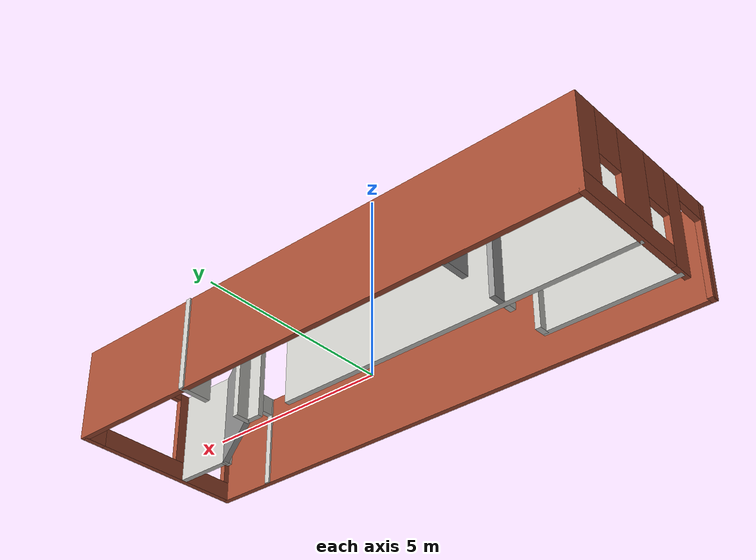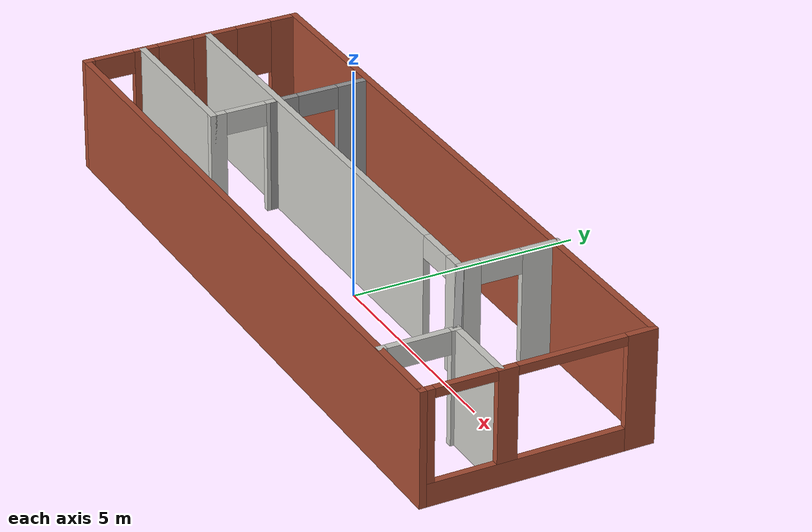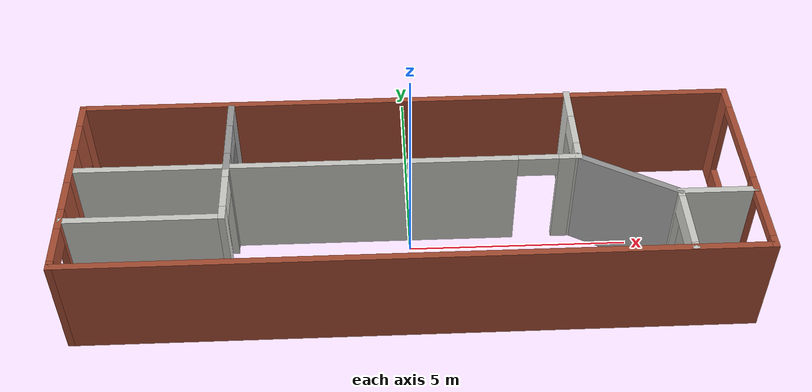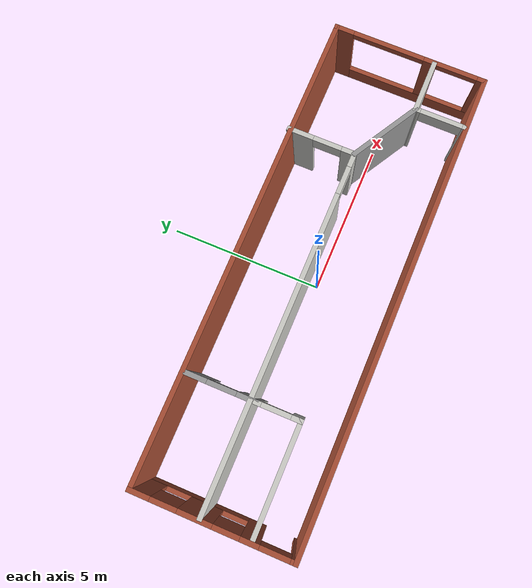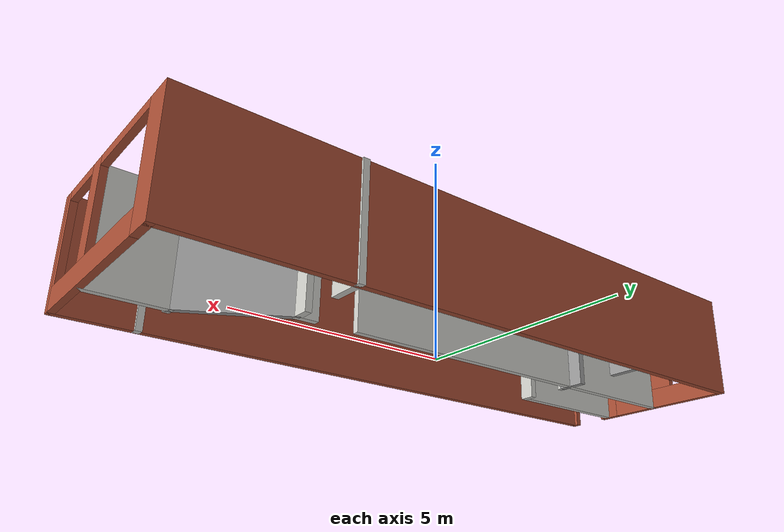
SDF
<?xml version='1.0'?>
<sdf version='1.6'>
  <model name='buildingMyHouse'>
    <link name='Wall_33'>
      <pose frame=''>0 -2.44789 0 0 -0 3.14159</pose>
      <self_collide>0</self_collide>
      <kinematic>0</kinematic>
      <visual name='Wall_33_Visual'>
        <pose frame=''>0 0 1.25 0 -0 0</pose>
        <geometry>
          <box>
            <size>15 0.15 2.5</size>
          </box>
        </geometry>
        <material>
          <script>
            <uri>file://media/materials/scripts/gazebo.material</uri>
            <name>Gazebo/Bricks</name>
          </script>
          <ambient>1 1 1 1</ambient>
          <shader type='pixel'/>
          <diffuse>1 1 1 1</diffuse>
          <specular>0.2 0.2 0.2 1</specular>
          <emissive>0 0 0 1</emissive>
        </material>
        <meta>
          <layer>0</layer>
        </meta>
        <transparency>0</transparency>
        <cast_shadows>1</cast_shadows>
      </visual>
      <collision name='Wall_33_Collision'>
        <laser_retro>0</laser_retro>
        <max_contacts>10</max_contacts>
        <pose frame=''>0 0 1.25 0 -0 0</pose>
        <geometry>
          <box>
            <size>15 0.15 2.5</size>
          </box>
        </geometry>
        <surface>
          <friction>
            <ode>
              <mu>1</mu>
              <mu2>1</mu2>
              <fdir1>0 0 0</fdir1>
              <slip1>0</slip1>
              <slip2>0</slip2>
            </ode>
            <torsional>
              <coefficient>1</coefficient>
              <patch_radius>0</patch_radius>
              <surface_radius>0</surface_radius>
              <use_patch_radius>1</use_patch_radius>
              <ode>
                <slip>0</slip>
              </ode>
            </torsional>
          </friction>
          <bounce>
            <restitution_coefficient>0</restitution_coefficient>
            <threshold>1e+06</threshold>
          </bounce>
          <contact>
            <collide_without_contact>0</collide_without_contact>
            <collide_without_contact_bitmask>1</collide_without_contact_bitmask>
            <collide_bitmask>1</collide_bitmask>
            <ode>
              <soft_cfm>0</soft_cfm>
              <soft_erp>0.2</soft_erp>
              <kp>1e+13</kp>
              <kd>1</kd>
              <max_vel>0.01</max_vel>
              <min_depth>0</min_depth>
            </ode>
            <bullet>
              <split_impulse>1</split_impulse>
              <split_impulse_penetration_threshold>-0.01</split_impulse_penetration_threshold>
              <soft_cfm>0</soft_cfm>
              <soft_erp>0.2</soft_erp>
              <kp>1e+13</kp>
              <kd>1</kd>
            </bullet>
          </contact>
        </surface>
      </collision>
    </link>
    <link name='Wall_34'>
      <pose frame=''>-7.425 -0.022893 0 0 -0 1.5708</pose>
      <self_collide>0</self_collide>
      <kinematic>0</kinematic>
      <visual name='Wall_34_Visual_0'>
        <pose frame=''>-2.38147 0 1.25 0 -0 0</pose>
        <geometry>
          <box>
            <size>0.237054 0.15 2.5</size>
          </box>
        </geometry>
        <material>
          <script>
            <uri>file://media/materials/scripts/gazebo.material</uri>
            <name>Gazebo/Bricks</name>
          </script>
          <ambient>1 1 1 1</ambient>
          <shader type='pixel'/>
          <diffuse>1 1 1 1</diffuse>
          <specular>0.2 0.2 0.2 1</specular>
          <emissive>0 0 0 1</emissive>
        </material>
        <meta>
          <layer>0</layer>
        </meta>
        <transparency>0</transparency>
        <cast_shadows>1</cast_shadows>
      </visual>
      <visual name='Wall_34_Visual_1'>
        <pose frame=''>-1.08246 0 1.25 0 -0 0</pose>
        <geometry>
          <box>
            <size>0.560967 0.15 2.5</size>
          </box>
        </geometry>
        <material>
          <script>
            <uri>file://media/materials/scripts/gazebo.material</uri>
            <name>Gazebo/Bricks</name>
          </script>
          <ambient>1 1 1 1</ambient>
          <shader type='pixel'/>
          <diffuse>1 1 1 1</diffuse>
          <specular>0.2 0.2 0.2 1</specular>
          <emissive>0 0 0 1</emissive>
        </material>
        <meta>
          <layer>0</layer>
        </meta>
        <transparency>0</transparency>
        <cast_shadows>1</cast_shadows>
      </visual>
      <visual name='Wall_34_Visual_2'>
        <pose frame=''>0.849011 0 0.25 0 -0 0</pose>
        <geometry>
          <box>
            <size>3.30198 0.15 0.5</size>
          </box>
        </geometry>
        <material>
          <script>
            <uri>file://media/materials/scripts/gazebo.material</uri>
            <name>Gazebo/Bricks</name>
          </script>
          <ambient>1 1 1 1</ambient>
          <shader type='pixel'/>
          <diffuse>1 1 1 1</diffuse>
          <specular>0.2 0.2 0.2 1</specular>
          <emissive>0 0 0 1</emissive>
        </material>
        <meta>
          <layer>0</layer>
        </meta>
        <transparency>0</transparency>
        <cast_shadows>1</cast_shadows>
      </visual>
      <visual name='Wall_34_Visual_3'>
        <pose frame=''>0.51168 0 1.5 0 -0 0</pose>
        <geometry>
          <box>
            <size>1.02732 0.15 2</size>
          </box>
        </geometry>
        <material>
          <script>
            <uri>file://media/materials/scripts/gazebo.material</uri>
            <name>Gazebo/Bricks</name>
          </script>
          <ambient>1 1 1 1</ambient>
          <shader type='pixel'/>
          <diffuse>1 1 1 1</diffuse>
          <specular>0.2 0.2 0.2 1</specular>
          <emissive>0 0 0 1</emissive>
        </material>
        <meta>
          <layer>0</layer>
        </meta>
        <transparency>0</transparency>
        <cast_shadows>1</cast_shadows>
      </visual>
      <visual name='Wall_34_Visual_4'>
        <pose frame=''>2.16267 0 1.5 0 -0 0</pose>
        <geometry>
          <box>
            <size>0.674661 0.15 2</size>
          </box>
        </geometry>
        <material>
          <script>
            <uri>file://media/materials/scripts/gazebo.material</uri>
            <name>Gazebo/Bricks</name>
          </script>
          <ambient>1 1 1 1</ambient>
          <shader type='pixel'/>
          <diffuse>1 1 1 1</diffuse>
          <specular>0.2 0.2 0.2 1</specular>
          <emissive>0 0 0 1</emissive>
        </material>
        <meta>
          <layer>0</layer>
        </meta>
        <transparency>0</transparency>
        <cast_shadows>1</cast_shadows>
      </visual>
      <visual name='Wall_34_Visual_5'>
        <pose frame=''>-0.401979 0 1.9 0 -0 0</pose>
        <geometry>
          <box>
            <size>0.8 0.15 1.2</size>
          </box>
        </geometry>
        <material>
          <script>
            <uri>file://media/materials/scripts/gazebo.material</uri>
            <name>Gazebo/Bricks</name>
          </script>
          <ambient>1 1 1 1</ambient>
          <shader type='pixel'/>
          <diffuse>1 1 1 1</diffuse>
          <specular>0.2 0.2 0.2 1</specular>
          <emissive>0 0 0 1</emissive>
        </material>
        <meta>
          <layer>0</layer>
        </meta>
        <transparency>0</transparency>
        <cast_shadows>1</cast_shadows>
      </visual>
      <visual name='Wall_34_Visual_6'>
        <pose frame=''>1.42534 0 1.9 0 -0 0</pose>
        <geometry>
          <box>
            <size>0.8 0.15 1.2</size>
          </box>
        </geometry>
        <material>
          <script>
            <uri>file://media/materials/scripts/gazebo.material</uri>
            <name>Gazebo/Bricks</name>
          </script>
          <ambient>1 1 1 1</ambient>
          <shader type='pixel'/>
          <diffuse>1 1 1 1</diffuse>
          <specular>0.2 0.2 0.2 1</specular>
          <emissive>0 0 0 1</emissive>
        </material>
        <meta>
          <layer>0</layer>
        </meta>
        <transparency>0</transparency>
        <cast_shadows>1</cast_shadows>
      </visual>
      <visual name='Wall_34_Visual_7'>
        <pose frame=''>-1.81295 0 2.25 0 -0 0</pose>
        <geometry>
          <box>
            <size>0.9 0.15 0.5</size>
          </box>
        </geometry>
        <material>
          <script>
            <uri>file://media/materials/scripts/gazebo.material</uri>
            <name>Gazebo/Bricks</name>
          </script>
          <ambient>1 1 1 1</ambient>
          <shader type='pixel'/>
          <diffuse>1 1 1 1</diffuse>
          <specular>0.2 0.2 0.2 1</specular>
          <emissive>0 0 0 1</emissive>
        </material>
        <meta>
          <layer>0</layer>
        </meta>
        <transparency>0</transparency>
        <cast_shadows>1</cast_shadows>
      </visual>
      <collision name='Wall_34_Collision_0'>
        <laser_retro>0</laser_retro>
        <max_contacts>10</max_contacts>
        <pose frame=''>-2.38147 0 1.25 0 -0 0</pose>
        <geometry>
          <box>
            <size>0.237054 0.15 2.5</size>
          </box>
        </geometry>
        <surface>
          <friction>
            <ode>
              <mu>1</mu>
              <mu2>1</mu2>
              <fdir1>0 0 0</fdir1>
              <slip1>0</slip1>
              <slip2>0</slip2>
            </ode>
            <torsional>
              <coefficient>1</coefficient>
              <patch_radius>0</patch_radius>
              <surface_radius>0</surface_radius>
              <use_patch_radius>1</use_patch_radius>
              <ode>
                <slip>0</slip>
              </ode>
            </torsional>
          </friction>
          <bounce>
            <restitution_coefficient>0</restitution_coefficient>
            <threshold>1e+06</threshold>
          </bounce>
          <contact>
            <collide_without_contact>0</collide_without_contact>
            <collide_without_contact_bitmask>1</collide_without_contact_bitmask>
            <collide_bitmask>1</collide_bitmask>
            <ode>
              <soft_cfm>0</soft_cfm>
              <soft_erp>0.2</soft_erp>
              <kp>1e+13</kp>
              <kd>1</kd>
              <max_vel>0.01</max_vel>
              <min_depth>0</min_depth>
            </ode>
            <bullet>
              <split_impulse>1</split_impulse>
              <split_impulse_penetration_threshold>-0.01</split_impulse_penetration_threshold>
              <soft_cfm>0</soft_cfm>
              <soft_erp>0.2</soft_erp>
              <kp>1e+13</kp>
              <kd>1</kd>
            </bullet>
          </contact>
        </surface>
      </collision>
      <collision name='Wall_34_Collision_1'>
        <laser_retro>0</laser_retro>
        <max_contacts>10</max_contacts>
        <pose frame=''>-1.08246 0 1.25 0 -0 0</pose>
        <geometry>
          <box>
            <size>0.560967 0.15 2.5</size>
          </box>
        </geometry>
        <surface>
          <friction>
            <ode>
              <mu>1</mu>
              <mu2>1</mu2>
              <fdir1>0 0 0</fdir1>
              <slip1>0</slip1>
              <slip2>0</slip2>
            </ode>
            <torsional>
              <coefficient>1</coefficient>
              <patch_radius>0</patch_radius>
              <surface_radius>0</surface_radius>
              <use_patch_radius>1</use_patch_radius>
              <ode>
                <slip>0</slip>
              </ode>
            </torsional>
          </friction>
          <bounce>
            <restitution_coefficient>0</restitution_coefficient>
            <threshold>1e+06</threshold>
          </bounce>
          <contact>
            <collide_without_contact>0</collide_without_contact>
            <collide_without_contact_bitmask>1</collide_without_contact_bitmask>
            <collide_bitmask>1</collide_bitmask>
            <ode>
              <soft_cfm>0</soft_cfm>
              <soft_erp>0.2</soft_erp>
              <kp>1e+13</kp>
              <kd>1</kd>
              <max_vel>0.01</max_vel>
              <min_depth>0</min_depth>
            </ode>
            <bullet>
              <split_impulse>1</split_impulse>
              <split_impulse_penetration_threshold>-0.01</split_impulse_penetration_threshold>
              <soft_cfm>0</soft_cfm>
              <soft_erp>0.2</soft_erp>
              <kp>1e+13</kp>
              <kd>1</kd>
            </bullet>
          </contact>
        </surface>
      </collision>
      <collision name='Wall_34_Collision_2'>
        <laser_retro>0</laser_retro>
        <max_contacts>10</max_contacts>
        <pose frame=''>0.849011 0 0.25 0 -0 0</pose>
        <geometry>
          <box>
            <size>3.30198 0.15 0.5</size>
          </box>
        </geometry>
        <surface>
          <friction>
            <ode>
              <mu>1</mu>
              <mu2>1</mu2>
              <fdir1>0 0 0</fdir1>
              <slip1>0</slip1>
              <slip2>0</slip2>
            </ode>
            <torsional>
              <coefficient>1</coefficient>
              <patch_radius>0</patch_radius>
              <surface_radius>0</surface_radius>
              <use_patch_radius>1</use_patch_radius>
              <ode>
                <slip>0</slip>
              </ode>
            </torsional>
          </friction>
          <bounce>
            <restitution_coefficient>0</restitution_coefficient>
            <threshold>1e+06</threshold>
          </bounce>
          <contact>
            <collide_without_contact>0</collide_without_contact>
            <collide_without_contact_bitmask>1</collide_without_contact_bitmask>
            <collide_bitmask>1</collide_bitmask>
            <ode>
              <soft_cfm>0</soft_cfm>
              <soft_erp>0.2</soft_erp>
              <kp>1e+13</kp>
              <kd>1</kd>
              <max_vel>0.01</max_vel>
              <min_depth>0</min_depth>
            </ode>
            <bullet>
              <split_impulse>1</split_impulse>
              <split_impulse_penetration_threshold>-0.01</split_impulse_penetration_threshold>
              <soft_cfm>0</soft_cfm>
              <soft_erp>0.2</soft_erp>
              <kp>1e+13</kp>
              <kd>1</kd>
            </bullet>
          </contact>
        </surface>
      </collision>
      <collision name='Wall_34_Collision_3'>
        <laser_retro>0</laser_retro>
        <max_contacts>10</max_contacts>
        <pose frame=''>0.51168 0 1.5 0 -0 0</pose>
        <geometry>
          <box>
            <size>1.02732 0.15 2</size>
          </box>
        </geometry>
        <surface>
          <friction>
            <ode>
              <mu>1</mu>
              <mu2>1</mu2>
              <fdir1>0 0 0</fdir1>
              <slip1>0</slip1>
              <slip2>0</slip2>
            </ode>
            <torsional>
              <coefficient>1</coefficient>
              <patch_radius>0</patch_radius>
              <surface_radius>0</surface_radius>
              <use_patch_radius>1</use_patch_radius>
              <ode>
                <slip>0</slip>
              </ode>
            </torsional>
          </friction>
          <bounce>
            <restitution_coefficient>0</restitution_coefficient>
            <threshold>1e+06</threshold>
          </bounce>
          <contact>
            <collide_without_contact>0</collide_without_contact>
            <collide_without_contact_bitmask>1</collide_without_contact_bitmask>
            <collide_bitmask>1</collide_bitmask>
            <ode>
              <soft_cfm>0</soft_cfm>
              <soft_erp>0.2</soft_erp>
              <kp>1e+13</kp>
              <kd>1</kd>
              <max_vel>0.01</max_vel>
              <min_depth>0</min_depth>
            </ode>
            <bullet>
              <split_impulse>1</split_impulse>
              <split_impulse_penetration_threshold>-0.01</split_impulse_penetration_threshold>
              <soft_cfm>0</soft_cfm>
              <soft_erp>0.2</soft_erp>
              <kp>1e+13</kp>
              <kd>1</kd>
            </bullet>
          </contact>
        </surface>
      </collision>
      <collision name='Wall_34_Collision_4'>
        <laser_retro>0</laser_retro>
        <max_contacts>10</max_contacts>
        <pose frame=''>2.16267 0 1.5 0 -0 0</pose>
        <geometry>
          <box>
            <size>0.674661 0.15 2</size>
          </box>
        </geometry>
        <surface>
          <friction>
            <ode>
              <mu>1</mu>
              <mu2>1</mu2>
              <fdir1>0 0 0</fdir1>
              <slip1>0</slip1>
              <slip2>0</slip2>
            </ode>
            <torsional>
              <coefficient>1</coefficient>
              <patch_radius>0</patch_radius>
              <surface_radius>0</surface_radius>
              <use_patch_radius>1</use_patch_radius>
              <ode>
                <slip>0</slip>
              </ode>
            </torsional>
          </friction>
          <bounce>
            <restitution_coefficient>0</restitution_coefficient>
            <threshold>1e+06</threshold>
          </bounce>
          <contact>
            <collide_without_contact>0</collide_without_contact>
            <collide_without_contact_bitmask>1</collide_without_contact_bitmask>
            <collide_bitmask>1</collide_bitmask>
            <ode>
              <soft_cfm>0</soft_cfm>
              <soft_erp>0.2</soft_erp>
              <kp>1e+13</kp>
              <kd>1</kd>
              <max_vel>0.01</max_vel>
              <min_depth>0</min_depth>
            </ode>
            <bullet>
              <split_impulse>1</split_impulse>
              <split_impulse_penetration_threshold>-0.01</split_impulse_penetration_threshold>
              <soft_cfm>0</soft_cfm>
              <soft_erp>0.2</soft_erp>
              <kp>1e+13</kp>
              <kd>1</kd>
            </bullet>
          </contact>
        </surface>
      </collision>
      <collision name='Wall_34_Collision_5'>
        <laser_retro>0</laser_retro>
        <max_contacts>10</max_contacts>
        <pose frame=''>-0.401979 0 1.9 0 -0 0</pose>
        <geometry>
          <box>
            <size>0.8 0.15 1.2</size>
          </box>
        </geometry>
        <surface>
          <friction>
            <ode>
              <mu>1</mu>
              <mu2>1</mu2>
              <fdir1>0 0 0</fdir1>
              <slip1>0</slip1>
              <slip2>0</slip2>
            </ode>
            <torsional>
              <coefficient>1</coefficient>
              <patch_radius>0</patch_radius>
              <surface_radius>0</surface_radius>
              <use_patch_radius>1</use_patch_radius>
              <ode>
                <slip>0</slip>
              </ode>
            </torsional>
          </friction>
          <bounce>
            <restitution_coefficient>0</restitution_coefficient>
            <threshold>1e+06</threshold>
          </bounce>
          <contact>
            <collide_without_contact>0</collide_without_contact>
            <collide_without_contact_bitmask>1</collide_without_contact_bitmask>
            <collide_bitmask>1</collide_bitmask>
            <ode>
              <soft_cfm>0</soft_cfm>
              <soft_erp>0.2</soft_erp>
              <kp>1e+13</kp>
              <kd>1</kd>
              <max_vel>0.01</max_vel>
              <min_depth>0</min_depth>
            </ode>
            <bullet>
              <split_impulse>1</split_impulse>
              <split_impulse_penetration_threshold>-0.01</split_impulse_penetration_threshold>
              <soft_cfm>0</soft_cfm>
              <soft_erp>0.2</soft_erp>
              <kp>1e+13</kp>
              <kd>1</kd>
            </bullet>
          </contact>
        </surface>
      </collision>
      <collision name='Wall_34_Collision_6'>
        <laser_retro>0</laser_retro>
        <max_contacts>10</max_contacts>
        <pose frame=''>1.42534 0 1.9 0 -0 0</pose>
        <geometry>
          <box>
            <size>0.8 0.15 1.2</size>
          </box>
        </geometry>
        <surface>
          <friction>
            <ode>
              <mu>1</mu>
              <mu2>1</mu2>
              <fdir1>0 0 0</fdir1>
              <slip1>0</slip1>
              <slip2>0</slip2>
            </ode>
            <torsional>
              <coefficient>1</coefficient>
              <patch_radius>0</patch_radius>
              <surface_radius>0</surface_radius>
              <use_patch_radius>1</use_patch_radius>
              <ode>
                <slip>0</slip>
              </ode>
            </torsional>
          </friction>
          <bounce>
            <restitution_coefficient>0</restitution_coefficient>
            <threshold>1e+06</threshold>
          </bounce>
          <contact>
            <collide_without_contact>0</collide_without_contact>
            <collide_without_contact_bitmask>1</collide_without_contact_bitmask>
            <collide_bitmask>1</collide_bitmask>
            <ode>
              <soft_cfm>0</soft_cfm>
              <soft_erp>0.2</soft_erp>
              <kp>1e+13</kp>
              <kd>1</kd>
              <max_vel>0.01</max_vel>
              <min_depth>0</min_depth>
            </ode>
            <bullet>
              <split_impulse>1</split_impulse>
              <split_impulse_penetration_threshold>-0.01</split_impulse_penetration_threshold>
              <soft_cfm>0</soft_cfm>
              <soft_erp>0.2</soft_erp>
              <kp>1e+13</kp>
              <kd>1</kd>
            </bullet>
          </contact>
        </surface>
      </collision>
      <collision name='Wall_34_Collision_7'>
        <laser_retro>0</laser_retro>
        <max_contacts>10</max_contacts>
        <pose frame=''>-1.81295 0 2.25 0 -0 0</pose>
        <geometry>
          <box>
            <size>0.9 0.15 0.5</size>
          </box>
        </geometry>
        <surface>
          <friction>
            <ode>
              <mu>1</mu>
              <mu2>1</mu2>
              <fdir1>0 0 0</fdir1>
              <slip1>0</slip1>
              <slip2>0</slip2>
            </ode>
            <torsional>
              <coefficient>1</coefficient>
              <patch_radius>0</patch_radius>
              <surface_radius>0</surface_radius>
              <use_patch_radius>1</use_patch_radius>
              <ode>
                <slip>0</slip>
              </ode>
            </torsional>
          </friction>
          <bounce>
            <restitution_coefficient>0</restitution_coefficient>
            <threshold>1e+06</threshold>
          </bounce>
          <contact>
            <collide_without_contact>0</collide_without_contact>
            <collide_without_contact_bitmask>1</collide_without_contact_bitmask>
            <collide_bitmask>1</collide_bitmask>
            <ode>
              <soft_cfm>0</soft_cfm>
              <soft_erp>0.2</soft_erp>
              <kp>1e+13</kp>
              <kd>1</kd>
              <max_vel>0.01</max_vel>
              <min_depth>0</min_depth>
            </ode>
            <bullet>
              <split_impulse>1</split_impulse>
              <split_impulse_penetration_threshold>-0.01</split_impulse_penetration_threshold>
              <soft_cfm>0</soft_cfm>
              <soft_erp>0.2</soft_erp>
              <kp>1e+13</kp>
              <kd>1</kd>
            </bullet>
          </contact>
        </surface>
      </collision>
    </link>
    <link name='Wall_35'>
      <pose frame=''>0 2.40211 0 0 -0 0</pose>
      <self_collide>0</self_collide>
      <kinematic>0</kinematic>
      <visual name='Wall_35_Visual'>
        <pose frame=''>0 0 1.25 0 -0 0</pose>
        <geometry>
          <box>
            <size>15 0.15 2.5</size>
          </box>
        </geometry>
        <material>
          <script>
            <uri>file://media/materials/scripts/gazebo.material</uri>
            <name>Gazebo/Bricks</name>
          </script>
          <ambient>1 1 1 1</ambient>
          <shader type='pixel'/>
          <diffuse>1 1 1 1</diffuse>
          <specular>0.2 0.2 0.2 1</specular>
          <emissive>0 0 0 1</emissive>
        </material>
        <meta>
          <layer>0</layer>
        </meta>
        <transparency>0</transparency>
        <cast_shadows>1</cast_shadows>
      </visual>
      <collision name='Wall_35_Collision'>
        <laser_retro>0</laser_retro>
        <max_contacts>10</max_contacts>
        <pose frame=''>0 0 1.25 0 -0 0</pose>
        <geometry>
          <box>
            <size>15 0.15 2.5</size>
          </box>
        </geometry>
        <surface>
          <friction>
            <ode>
              <mu>1</mu>
              <mu2>1</mu2>
              <fdir1>0 0 0</fdir1>
              <slip1>0</slip1>
              <slip2>0</slip2>
            </ode>
            <torsional>
              <coefficient>1</coefficient>
              <patch_radius>0</patch_radius>
              <surface_radius>0</surface_radius>
              <use_patch_radius>1</use_patch_radius>
              <ode>
                <slip>0</slip>
              </ode>
            </torsional>
          </friction>
          <bounce>
            <restitution_coefficient>0</restitution_coefficient>
            <threshold>1e+06</threshold>
          </bounce>
          <contact>
            <collide_without_contact>0</collide_without_contact>
            <collide_without_contact_bitmask>1</collide_without_contact_bitmask>
            <collide_bitmask>1</collide_bitmask>
            <ode>
              <soft_cfm>0</soft_cfm>
              <soft_erp>0.2</soft_erp>
              <kp>1e+13</kp>
              <kd>1</kd>
              <max_vel>0.01</max_vel>
              <min_depth>0</min_depth>
            </ode>
            <bullet>
              <split_impulse>1</split_impulse>
              <split_impulse_penetration_threshold>-0.01</split_impulse_penetration_threshold>
              <soft_cfm>0</soft_cfm>
              <soft_erp>0.2</soft_erp>
              <kp>1e+13</kp>
              <kd>1</kd>
            </bullet>
          </contact>
        </surface>
      </collision>
    </link>
    <link name='Wall_40'>
      <pose frame=''>-1.80848 0.347893 0 0 -0 0</pose>
      <self_collide>0</self_collide>
      <kinematic>0</kinematic>
      <visual name='Wall_40_Visual_0'>
        <pose frame=''>-0.709013 0 1.25 0 -0 0</pose>
        <geometry>
          <box>
            <size>9.83197 0.15 2.5</size>
          </box>
        </geometry>
        <material>
          <script>
            <uri>file://media/materials/scripts/gazebo.material</uri>
            <name>Gazebo/CeilingTiled</name>
          </script>
          <ambient>1 1 1 1</ambient>
          <shader type='pixel'/>
          <diffuse>1 1 1 1</diffuse>
          <specular>0 0 0 1</specular>
          <emissive>0 0 0 1</emissive>
        </material>
        <meta>
          <layer>0</layer>
        </meta>
        <transparency>0</transparency>
        <cast_shadows>1</cast_shadows>
      </visual>
      <visual name='Wall_40_Visual_1'>
        <pose frame=''>5.36599 0 1.25 0 -0 0</pose>
        <geometry>
          <box>
            <size>0.518027 0.15 2.5</size>
          </box>
        </geometry>
        <material>
          <script>
            <uri>file://media/materials/scripts/gazebo.material</uri>
            <name>Gazebo/CeilingTiled</name>
          </script>
          <ambient>1 1 1 1</ambient>
          <shader type='pixel'/>
          <diffuse>1 1 1 1</diffuse>
          <specular>0 0 0 1</specular>
          <emissive>0 0 0 1</emissive>
        </material>
        <meta>
          <layer>0</layer>
        </meta>
        <transparency>0</transparency>
        <cast_shadows>1</cast_shadows>
      </visual>
      <visual name='Wall_40_Visual_2'>
        <pose frame=''>4.65697 0 2.25 0 -0 0</pose>
        <geometry>
          <box>
            <size>0.9 0.15 0.5</size>
          </box>
        </geometry>
        <material>
          <script>
            <uri>file://media/materials/scripts/gazebo.material</uri>
            <name>Gazebo/CeilingTiled</name>
          </script>
          <ambient>1 1 1 1</ambient>
          <shader type='pixel'/>
          <diffuse>1 1 1 1</diffuse>
          <specular>0 0 0 1</specular>
          <emissive>0 0 0 1</emissive>
        </material>
        <meta>
          <layer>0</layer>
        </meta>
        <transparency>0</transparency>
        <cast_shadows>1</cast_shadows>
      </visual>
      <collision name='Wall_40_Collision_0'>
        <laser_retro>0</laser_retro>
        <max_contacts>10</max_contacts>
        <pose frame=''>-0.709013 0 1.25 0 -0 0</pose>
        <geometry>
          <box>
            <size>9.83197 0.15 2.5</size>
          </box>
        </geometry>
        <surface>
          <friction>
            <ode>
              <mu>1</mu>
              <mu2>1</mu2>
              <fdir1>0 0 0</fdir1>
              <slip1>0</slip1>
              <slip2>0</slip2>
            </ode>
            <torsional>
              <coefficient>1</coefficient>
              <patch_radius>0</patch_radius>
              <surface_radius>0</surface_radius>
              <use_patch_radius>1</use_patch_radius>
              <ode>
                <slip>0</slip>
              </ode>
            </torsional>
          </friction>
          <bounce>
            <restitution_coefficient>0</restitution_coefficient>
            <threshold>1e+06</threshold>
          </bounce>
          <contact>
            <collide_without_contact>0</collide_without_contact>
            <collide_without_contact_bitmask>1</collide_without_contact_bitmask>
            <collide_bitmask>1</collide_bitmask>
            <ode>
              <soft_cfm>0</soft_cfm>
              <soft_erp>0.2</soft_erp>
              <kp>1e+13</kp>
              <kd>1</kd>
              <max_vel>0.01</max_vel>
              <min_depth>0</min_depth>
            </ode>
            <bullet>
              <split_impulse>1</split_impulse>
              <split_impulse_penetration_threshold>-0.01</split_impulse_penetration_threshold>
              <soft_cfm>0</soft_cfm>
              <soft_erp>0.2</soft_erp>
              <kp>1e+13</kp>
              <kd>1</kd>
            </bullet>
          </contact>
        </surface>
      </collision>
      <collision name='Wall_40_Collision_1'>
        <laser_retro>0</laser_retro>
        <max_contacts>10</max_contacts>
        <pose frame=''>5.36599 0 1.25 0 -0 0</pose>
        <geometry>
          <box>
            <size>0.518027 0.15 2.5</size>
          </box>
        </geometry>
        <surface>
          <friction>
            <ode>
              <mu>1</mu>
              <mu2>1</mu2>
              <fdir1>0 0 0</fdir1>
              <slip1>0</slip1>
              <slip2>0</slip2>
            </ode>
            <torsional>
              <coefficient>1</coefficient>
              <patch_radius>0</patch_radius>
              <surface_radius>0</surface_radius>
              <use_patch_radius>1</use_patch_radius>
              <ode>
                <slip>0</slip>
              </ode>
            </torsional>
          </friction>
          <bounce>
            <restitution_coefficient>0</restitution_coefficient>
            <threshold>1e+06</threshold>
          </bounce>
          <contact>
            <collide_without_contact>0</collide_without_contact>
            <collide_without_contact_bitmask>1</collide_without_contact_bitmask>
            <collide_bitmask>1</collide_bitmask>
            <ode>
              <soft_cfm>0</soft_cfm>
              <soft_erp>0.2</soft_erp>
              <kp>1e+13</kp>
              <kd>1</kd>
              <max_vel>0.01</max_vel>
              <min_depth>0</min_depth>
            </ode>
            <bullet>
              <split_impulse>1</split_impulse>
              <split_impulse_penetration_threshold>-0.01</split_impulse_penetration_threshold>
              <soft_cfm>0</soft_cfm>
              <soft_erp>0.2</soft_erp>
              <kp>1e+13</kp>
              <kd>1</kd>
            </bullet>
          </contact>
        </surface>
      </collision>
      <collision name='Wall_40_Collision_2'>
        <laser_retro>0</laser_retro>
        <max_contacts>10</max_contacts>
        <pose frame=''>4.65697 0 2.25 0 -0 0</pose>
        <geometry>
          <box>
            <size>0.9 0.15 0.5</size>
          </box>
        </geometry>
        <surface>
          <friction>
            <ode>
              <mu>1</mu>
              <mu2>1</mu2>
              <fdir1>0 0 0</fdir1>
              <slip1>0</slip1>
              <slip2>0</slip2>
            </ode>
            <torsional>
              <coefficient>1</coefficient>
              <patch_radius>0</patch_radius>
              <surface_radius>0</surface_radius>
              <use_patch_radius>1</use_patch_radius>
              <ode>
                <slip>0</slip>
              </ode>
            </torsional>
          </friction>
          <bounce>
            <restitution_coefficient>0</restitution_coefficient>
            <threshold>1e+06</threshold>
          </bounce>
          <contact>
            <collide_without_contact>0</collide_without_contact>
            <collide_without_contact_bitmask>1</collide_without_contact_bitmask>
            <collide_bitmask>1</collide_bitmask>
            <ode>
              <soft_cfm>0</soft_cfm>
              <soft_erp>0.2</soft_erp>
              <kp>1e+13</kp>
              <kd>1</kd>
              <max_vel>0.01</max_vel>
              <min_depth>0</min_depth>
            </ode>
            <bullet>
              <split_impulse>1</split_impulse>
              <split_impulse_penetration_threshold>-0.01</split_impulse_penetration_threshold>
              <soft_cfm>0</soft_cfm>
              <soft_erp>0.2</soft_erp>
              <kp>1e+13</kp>
              <kd>1</kd>
            </bullet>
          </contact>
        </surface>
      </collision>
    </link>
    <link name='Wall_43'>
      <pose frame=''>4.7591 -0.239607 0 0 0 -0.523599</pose>
      <self_collide>0</self_collide>
      <kinematic>0</kinematic>
      <visual name='Wall_43_Visual'>
        <pose frame=''>0 0 1.25 0 -0 0</pose>
        <geometry>
          <box>
            <size>2.5 0.15 2.5</size>
          </box>
        </geometry>
        <material>
          <script>
            <uri>file://media/materials/scripts/gazebo.material</uri>
            <name>Gazebo/Grey</name>
          </script>
          <ambient>1 1 1 1</ambient>
          <shader type='pixel'/>
          <diffuse>0.7 0.7 0.7 1</diffuse>
          <specular>0.01 0.01 0.01 1</specular>
          <emissive>0 0 0 1</emissive>
        </material>
        <meta>
          <layer>0</layer>
        </meta>
        <transparency>0</transparency>
        <cast_shadows>1</cast_shadows>
      </visual>
      <collision name='Wall_43_Collision'>
        <laser_retro>0</laser_retro>
        <max_contacts>10</max_contacts>
        <pose frame=''>0 0 1.25 0 -0 0</pose>
        <geometry>
          <box>
            <size>2.5 0.15 2.5</size>
          </box>
        </geometry>
        <surface>
          <friction>
            <ode>
              <mu>1</mu>
              <mu2>1</mu2>
              <fdir1>0 0 0</fdir1>
              <slip1>0</slip1>
              <slip2>0</slip2>
            </ode>
            <torsional>
              <coefficient>1</coefficient>
              <patch_radius>0</patch_radius>
              <surface_radius>0</surface_radius>
              <use_patch_radius>1</use_patch_radius>
              <ode>
                <slip>0</slip>
              </ode>
            </torsional>
          </friction>
          <bounce>
            <restitution_coefficient>0</restitution_coefficient>
            <threshold>1e+06</threshold>
          </bounce>
          <contact>
            <collide_without_contact>0</collide_without_contact>
            <collide_without_contact_bitmask>1</collide_without_contact_bitmask>
            <collide_bitmask>1</collide_bitmask>
            <ode>
              <soft_cfm>0</soft_cfm>
              <soft_erp>0.2</soft_erp>
              <kp>1e+13</kp>
              <kd>1</kd>
              <max_vel>0.01</max_vel>
              <min_depth>0</min_depth>
            </ode>
            <bullet>
              <split_impulse>1</split_impulse>
              <split_impulse_penetration_threshold>-0.01</split_impulse_penetration_threshold>
              <soft_cfm>0</soft_cfm>
              <soft_erp>0.2</soft_erp>
              <kp>1e+13</kp>
              <kd>1</kd>
            </bullet>
          </contact>
        </surface>
      </collision>
    </link>
    <link name='Wall_45'>
      <pose frame=''>-5.70023 -1.16505 0 0 -0 0</pose>
      <self_collide>0</self_collide>
      <kinematic>0</kinematic>
      <visual name='Wall_45_Visual'>
        <pose frame=''>0 0 1.25 0 -0 0</pose>
        <geometry>
          <box>
            <size>3.5 0.15 2.5</size>
          </box>
        </geometry>
        <material>
          <script>
            <uri>file://media/materials/scripts/gazebo.material</uri>
            <name>Gazebo/CeilingTiled</name>
          </script>
          <ambient>1 1 1 1</ambient>
          <shader type='pixel'/>
          <diffuse>1 1 1 1</diffuse>
          <specular>0 0 0 1</specular>
          <emissive>0 0 0 1</emissive>
        </material>
        <meta>
          <layer>0</layer>
        </meta>
        <transparency>0</transparency>
        <cast_shadows>1</cast_shadows>
      </visual>
      <collision name='Wall_45_Collision'>
        <laser_retro>0</laser_retro>
        <max_contacts>10</max_contacts>
        <pose frame=''>0 0 1.25 0 -0 0</pose>
        <geometry>
          <box>
            <size>3.5 0.15 2.5</size>
          </box>
        </geometry>
        <surface>
          <friction>
            <ode>
              <mu>1</mu>
              <mu2>1</mu2>
              <fdir1>0 0 0</fdir1>
              <slip1>0</slip1>
              <slip2>0</slip2>
            </ode>
            <torsional>
              <coefficient>1</coefficient>
              <patch_radius>0</patch_radius>
              <surface_radius>0</surface_radius>
              <use_patch_radius>1</use_patch_radius>
              <ode>
                <slip>0</slip>
              </ode>
            </torsional>
          </friction>
          <bounce>
            <restitution_coefficient>0</restitution_coefficient>
            <threshold>1e+06</threshold>
          </bounce>
          <contact>
            <collide_without_contact>0</collide_without_contact>
            <collide_without_contact_bitmask>1</collide_without_contact_bitmask>
            <collide_bitmask>1</collide_bitmask>
            <ode>
              <soft_cfm>0</soft_cfm>
              <soft_erp>0.2</soft_erp>
              <kp>1e+13</kp>
              <kd>1</kd>
              <max_vel>0.01</max_vel>
              <min_depth>0</min_depth>
            </ode>
            <bullet>
              <split_impulse>1</split_impulse>
              <split_impulse_penetration_threshold>-0.01</split_impulse_penetration_threshold>
              <soft_cfm>0</soft_cfm>
              <soft_erp>0.2</soft_erp>
              <kp>1e+13</kp>
              <kd>1</kd>
            </bullet>
          </contact>
        </surface>
      </collision>
    </link>
    <link name='Wall_46'>
      <pose frame=''>-4.02523 -0.490052 0 0 -0 1.5708</pose>
      <self_collide>0</self_collide>
      <kinematic>0</kinematic>
      <gravity>1</gravity>
      <inertial>
        <mass>1</mass>
        <pose frame=''>0 0 0 0 -0 0</pose>
        <inertia>
          <ixx>1</ixx>
          <ixy>0</ixy>
          <ixz>0</ixz>
          <iyy>1</iyy>
          <iyz>0</iyz>
          <izz>1</izz>
        </inertia>
      </inertial>
      <visual name='Wall_46_Visual_0'>
        <pose frame=''>-0.56741 0 1.25 0 -0 0</pose>
        <geometry>
          <box>
            <size>0.365179 0.15 2.5</size>
          </box>
        </geometry>
        <material>
          <script>
            <uri>file://media/materials/scripts/gazebo.material</uri>
            <name>Gazebo/CeilingTiled</name>
          </script>
          <ambient>0.9 0 0 1</ambient>
          <shader type='pixel'>
            <normal_map>__default__</normal_map>
          </shader>
          <diffuse>0.9 0 0 1</diffuse>
          <specular>0.9 0 0 1</specular>
          <emissive>0 0 0 1</emissive>
        </material>
        <meta>
          <layer>0</layer>
        </meta>
        <transparency>0</transparency>
        <cast_shadows>1</cast_shadows>
      </visual>
      <visual name='Wall_46_Visual_1'>
        <pose frame=''>0.63259 0 1.25 0 -0 0</pose>
        <geometry>
          <box>
            <size>0.234821 0.15 2.5</size>
          </box>
        </geometry>
        <material>
          <script>
            <uri>file://media/materials/scripts/gazebo.material</uri>
            <name>Gazebo/CeilingTiled</name>
          </script>
          <ambient>0.9 0 0 1</ambient>
          <shader type='pixel'>
            <normal_map>__default__</normal_map>
          </shader>
          <diffuse>0.9 0 0 1</diffuse>
          <specular>0 0 0 1</specular>
          <emissive>0 0 0 1</emissive>
        </material>
        <meta>
          <layer>0</layer>
        </meta>
        <transparency>0</transparency>
        <cast_shadows>1</cast_shadows>
      </visual>
      <visual name='Wall_46_Visual_2'>
        <pose frame=''>0.065179 0 2.25 0 -0 0</pose>
        <geometry>
          <box>
            <size>0.9 0.15 0.5</size>
          </box>
        </geometry>
        <material>
          <script>
            <uri>file://media/materials/scripts/gazebo.material</uri>
            <name>Gazebo/CeilingTiled</name>
          </script>
          <ambient>0.9 0 0 1</ambient>
          <shader type='pixel'>
            <normal_map>__default__</normal_map>
          </shader>
          <diffuse>0.9 0 0 1</diffuse>
          <specular>0 0 0 1</specular>
          <emissive>0 0 0 1</emissive>
        </material>
        <meta>
          <layer>0</layer>
        </meta>
        <transparency>0</transparency>
        <cast_shadows>1</cast_shadows>
      </visual>
      <collision name='Wall_46_Collision_2'>
        <laser_retro>0</laser_retro>
        <max_contacts>10</max_contacts>
        <pose frame=''>0.065179 0 2.25 0 -0 0</pose>
        <geometry>
          <box>
            <size>0.9 0.15 0.5</size>
          </box>
        </geometry>
        <surface>
          <friction>
            <ode>
              <mu>1</mu>
              <mu2>1</mu2>
              <fdir1>0 0 0</fdir1>
              <slip1>0</slip1>
              <slip2>0</slip2>
            </ode>
            <torsional>
              <coefficient>1</coefficient>
              <patch_radius>0</patch_radius>
              <surface_radius>0</surface_radius>
              <use_patch_radius>1</use_patch_radius>
              <ode>
                <slip>0</slip>
              </ode>
            </torsional>
          </friction>
          <bounce>
            <restitution_coefficient>0</restitution_coefficient>
            <threshold>1e+06</threshold>
          </bounce>
          <contact>
            <collide_without_contact>0</collide_without_contact>
            <collide_without_contact_bitmask>1</collide_without_contact_bitmask>
            <collide_bitmask>1</collide_bitmask>
            <ode>
              <soft_cfm>0</soft_cfm>
              <soft_erp>0.2</soft_erp>
              <kp>1e+13</kp>
              <kd>1</kd>
              <max_vel>0.01</max_vel>
              <min_depth>0</min_depth>
            </ode>
            <bullet>
              <split_impulse>1</split_impulse>
              <split_impulse_penetration_threshold>-0.01</split_impulse_penetration_threshold>
              <soft_cfm>0</soft_cfm>
              <soft_erp>0.2</soft_erp>
              <kp>1e+13</kp>
              <kd>1</kd>
            </bullet>
          </contact>
        </surface>
      </collision>
      <collision name='Wall_46_Collision_0'>
        <laser_retro>0</laser_retro>
        <max_contacts>10</max_contacts>
        <pose frame=''>-0.56741 0 1.25 0 -0 0</pose>
        <geometry>
          <box>
            <size>0.365179 0.15 2.5</size>
          </box>
        </geometry>
        <surface>
          <friction>
            <ode>
              <mu>1</mu>
              <mu2>1</mu2>
              <fdir1>0 0 0</fdir1>
              <slip1>0</slip1>
              <slip2>0</slip2>
            </ode>
            <torsional>
              <coefficient>1</coefficient>
              <patch_radius>0</patch_radius>
              <surface_radius>0</surface_radius>
              <use_patch_radius>1</use_patch_radius>
              <ode>
                <slip>0</slip>
              </ode>
            </torsional>
          </friction>
          <bounce>
            <restitution_coefficient>0</restitution_coefficient>
            <threshold>1e+06</threshold>
          </bounce>
          <contact>
            <collide_without_contact>0</collide_without_contact>
            <collide_without_contact_bitmask>1</collide_without_contact_bitmask>
            <collide_bitmask>1</collide_bitmask>
            <ode>
              <soft_cfm>0</soft_cfm>
              <soft_erp>0.2</soft_erp>
              <kp>1e+13</kp>
              <kd>1</kd>
              <max_vel>0.01</max_vel>
              <min_depth>0</min_depth>
            </ode>
            <bullet>
              <split_impulse>1</split_impulse>
              <split_impulse_penetration_threshold>-0.01</split_impulse_penetration_threshold>
              <soft_cfm>0</soft_cfm>
              <soft_erp>0.2</soft_erp>
              <kp>1e+13</kp>
              <kd>1</kd>
            </bullet>
          </contact>
        </surface>
      </collision>
      <collision name='Wall_46_Collision_1'>
        <laser_retro>0</laser_retro>
        <max_contacts>10</max_contacts>
        <pose frame=''>0.63259 0 1.25 0 -0 0</pose>
        <geometry>
          <box>
            <size>0.234821 0.15 2.5</size>
          </box>
        </geometry>
        <surface>
          <friction>
            <ode>
              <mu>1</mu>
              <mu2>1</mu2>
              <fdir1>0 0 0</fdir1>
              <slip1>0</slip1>
              <slip2>0</slip2>
            </ode>
            <torsional>
              <coefficient>1</coefficient>
              <patch_radius>0</patch_radius>
              <surface_radius>0</surface_radius>
              <use_patch_radius>1</use_patch_radius>
              <ode>
                <slip>0</slip>
              </ode>
            </torsional>
          </friction>
          <bounce>
            <restitution_coefficient>0</restitution_coefficient>
            <threshold>1e+06</threshold>
          </bounce>
          <contact>
            <collide_without_contact>0</collide_without_contact>
            <collide_without_contact_bitmask>1</collide_without_contact_bitmask>
            <collide_bitmask>1</collide_bitmask>
            <ode>
              <soft_cfm>0</soft_cfm>
              <soft_erp>0.2</soft_erp>
              <kp>1e+13</kp>
              <kd>1</kd>
              <max_vel>0.01</max_vel>
              <min_depth>0</min_depth>
            </ode>
            <bullet>
              <split_impulse>1</split_impulse>
              <split_impulse_penetration_threshold>-0.01</split_impulse_penetration_threshold>
              <soft_cfm>0</soft_cfm>
              <soft_erp>0.2</soft_erp>
              <kp>1e+13</kp>
              <kd>1</kd>
            </bullet>
          </contact>
        </surface>
      </collision>
    </link>
    <link name='Wall_47'>
      <pose frame=''>-4.02523 1.23495 0 0 -0 1.5708</pose>
      <self_collide>0</self_collide>
      <kinematic>0</kinematic>
      <visual name='Wall_47_Visual_0'>
        <pose frame=''>-0.796274 0 1.25 0 -0 0</pose>
        <geometry>
          <box>
            <size>0.657453 0.15 2.5</size>
          </box>
        </geometry>
        <material>
          <script>
            <uri>file://media/materials/scripts/gazebo.material</uri>
            <name>Gazebo/Grey</name>
          </script>
          <ambient>1 1 1 1</ambient>
          <shader type='pixel'/>
          <diffuse>0.7 0.7 0.7 1</diffuse>
          <specular>0.01 0.01 0.01 1</specular>
          <emissive>0 0 0 1</emissive>
        </material>
        <meta>
          <layer>0</layer>
        </meta>
        <transparency>0</transparency>
        <cast_shadows>1</cast_shadows>
      </visual>
      <visual name='Wall_47_Visual_1'>
        <pose frame=''>0.778726 0 1.25 0 -0 0</pose>
        <geometry>
          <box>
            <size>0.692547 0.15 2.5</size>
          </box>
        </geometry>
        <material>
          <script>
            <uri>file://media/materials/scripts/gazebo.material</uri>
            <name>Gazebo/Grey</name>
          </script>
          <ambient>1 1 1 1</ambient>
          <shader type='pixel'/>
          <diffuse>0.7 0.7 0.7 1</diffuse>
          <specular>0.01 0.01 0.01 1</specular>
          <emissive>0 0 0 1</emissive>
        </material>
        <meta>
          <layer>0</layer>
        </meta>
        <transparency>0</transparency>
        <cast_shadows>1</cast_shadows>
      </visual>
      <visual name='Wall_47_Visual_2'>
        <pose frame=''>-0.017547 0 2.25 0 -0 0</pose>
        <geometry>
          <box>
            <size>0.9 0.15 0.5</size>
          </box>
        </geometry>
        <material>
          <script>
            <uri>file://media/materials/scripts/gazebo.material</uri>
            <name>Gazebo/Grey</name>
          </script>
          <ambient>1 1 1 1</ambient>
          <shader type='pixel'/>
          <diffuse>0.7 0.7 0.7 1</diffuse>
          <specular>0.01 0.01 0.01 1</specular>
          <emissive>0 0 0 1</emissive>
        </material>
        <meta>
          <layer>0</layer>
        </meta>
        <transparency>0</transparency>
        <cast_shadows>1</cast_shadows>
      </visual>
      <collision name='Wall_47_Collision_0'>
        <laser_retro>0</laser_retro>
        <max_contacts>10</max_contacts>
        <pose frame=''>-0.796274 0 1.25 0 -0 0</pose>
        <geometry>
          <box>
            <size>0.657453 0.15 2.5</size>
          </box>
        </geometry>
        <surface>
          <friction>
            <ode>
              <mu>1</mu>
              <mu2>1</mu2>
              <fdir1>0 0 0</fdir1>
              <slip1>0</slip1>
              <slip2>0</slip2>
            </ode>
            <torsional>
              <coefficient>1</coefficient>
              <patch_radius>0</patch_radius>
              <surface_radius>0</surface_radius>
              <use_patch_radius>1</use_patch_radius>
              <ode>
                <slip>0</slip>
              </ode>
            </torsional>
          </friction>
          <bounce>
            <restitution_coefficient>0</restitution_coefficient>
            <threshold>1e+06</threshold>
          </bounce>
          <contact>
            <collide_without_contact>0</collide_without_contact>
            <collide_without_contact_bitmask>1</collide_without_contact_bitmask>
            <collide_bitmask>1</collide_bitmask>
            <ode>
              <soft_cfm>0</soft_cfm>
              <soft_erp>0.2</soft_erp>
              <kp>1e+13</kp>
              <kd>1</kd>
              <max_vel>0.01</max_vel>
              <min_depth>0</min_depth>
            </ode>
            <bullet>
              <split_impulse>1</split_impulse>
              <split_impulse_penetration_threshold>-0.01</split_impulse_penetration_threshold>
              <soft_cfm>0</soft_cfm>
              <soft_erp>0.2</soft_erp>
              <kp>1e+13</kp>
              <kd>1</kd>
            </bullet>
          </contact>
        </surface>
      </collision>
      <collision name='Wall_47_Collision_1'>
        <laser_retro>0</laser_retro>
        <max_contacts>10</max_contacts>
        <pose frame=''>0.778726 0 1.25 0 -0 0</pose>
        <geometry>
          <box>
            <size>0.692547 0.15 2.5</size>
          </box>
        </geometry>
        <surface>
          <friction>
            <ode>
              <mu>1</mu>
              <mu2>1</mu2>
              <fdir1>0 0 0</fdir1>
              <slip1>0</slip1>
              <slip2>0</slip2>
            </ode>
            <torsional>
              <coefficient>1</coefficient>
              <patch_radius>0</patch_radius>
              <surface_radius>0</surface_radius>
              <use_patch_radius>1</use_patch_radius>
              <ode>
                <slip>0</slip>
              </ode>
            </torsional>
          </friction>
          <bounce>
            <restitution_coefficient>0</restitution_coefficient>
            <threshold>1e+06</threshold>
          </bounce>
          <contact>
            <collide_without_contact>0</collide_without_contact>
            <collide_without_contact_bitmask>1</collide_without_contact_bitmask>
            <collide_bitmask>1</collide_bitmask>
            <ode>
              <soft_cfm>0</soft_cfm>
              <soft_erp>0.2</soft_erp>
              <kp>1e+13</kp>
              <kd>1</kd>
              <max_vel>0.01</max_vel>
              <min_depth>0</min_depth>
            </ode>
            <bullet>
              <split_impulse>1</split_impulse>
              <split_impulse_penetration_threshold>-0.01</split_impulse_penetration_threshold>
              <soft_cfm>0</soft_cfm>
              <soft_erp>0.2</soft_erp>
              <kp>1e+13</kp>
              <kd>1</kd>
            </bullet>
          </contact>
        </surface>
      </collision>
      <collision name='Wall_47_Collision_2'>
        <laser_retro>0</laser_retro>
        <max_contacts>10</max_contacts>
        <pose frame=''>-0.017547 0 2.25 0 -0 0</pose>
        <geometry>
          <box>
            <size>0.9 0.15 0.5</size>
          </box>
        </geometry>
        <surface>
          <friction>
            <ode>
              <mu>1</mu>
              <mu2>1</mu2>
              <fdir1>0 0 0</fdir1>
              <slip1>0</slip1>
              <slip2>0</slip2>
            </ode>
            <torsional>
              <coefficient>1</coefficient>
              <patch_radius>0</patch_radius>
              <surface_radius>0</surface_radius>
              <use_patch_radius>1</use_patch_radius>
              <ode>
                <slip>0</slip>
              </ode>
            </torsional>
          </friction>
          <bounce>
            <restitution_coefficient>0</restitution_coefficient>
            <threshold>1e+06</threshold>
          </bounce>
          <contact>
            <collide_without_contact>0</collide_without_contact>
            <collide_without_contact_bitmask>1</collide_without_contact_bitmask>
            <collide_bitmask>1</collide_bitmask>
            <ode>
              <soft_cfm>0</soft_cfm>
              <soft_erp>0.2</soft_erp>
              <kp>1e+13</kp>
              <kd>1</kd>
              <max_vel>0.01</max_vel>
              <min_depth>0</min_depth>
            </ode>
            <bullet>
              <split_impulse>1</split_impulse>
              <split_impulse_penetration_threshold>-0.01</split_impulse_penetration_threshold>
              <soft_cfm>0</soft_cfm>
              <soft_erp>0.2</soft_erp>
              <kp>1e+13</kp>
              <kd>1</kd>
            </bullet>
          </contact>
        </surface>
      </collision>
    </link>
    <link name='Wall_51'>
      <pose frame=''>7.425 -0.022893 0 0 0 -1.5708</pose>
      <self_collide>0</self_collide>
      <kinematic>0</kinematic>
      <visual name='Wall_51_Visual_0'>
        <pose frame=''>-2.17411 0 1.25 0 -0 0</pose>
        <geometry>
          <box>
            <size>0.651775 0.15 2.5</size>
          </box>
        </geometry>
        <material>
          <script>
            <uri>file://media/materials/scripts/gazebo.material</uri>
            <name>Gazebo/Bricks</name>
          </script>
          <ambient>1 1 1 1</ambient>
          <shader type='pixel'/>
          <diffuse>1 1 1 1</diffuse>
          <specular>0.2 0.2 0.2 1</specular>
          <emissive>0 0 0 1</emissive>
        </material>
        <meta>
          <layer>0</layer>
        </meta>
        <transparency>0</transparency>
        <cast_shadows>1</cast_shadows>
      </visual>
      <visual name='Wall_51_Visual_1'>
        <pose frame=''>0.325888 0 0.25 0 -0 0</pose>
        <geometry>
          <box>
            <size>4.34823 0.15 0.5</size>
          </box>
        </geometry>
        <material>
          <script>
            <uri>file://media/materials/scripts/gazebo.material</uri>
            <name>Gazebo/Bricks</name>
          </script>
          <ambient>1 1 1 1</ambient>
          <shader type='pixel'/>
          <diffuse>1 1 1 1</diffuse>
          <specular>0.2 0.2 0.2 1</specular>
          <emissive>0 0 0 1</emissive>
        </material>
        <meta>
          <layer>0</layer>
        </meta>
        <transparency>0</transparency>
        <cast_shadows>1</cast_shadows>
      </visual>
      <visual name='Wall_51_Visual_2'>
        <pose frame=''>0.670077 0 1.5 0 -0 0</pose>
        <geometry>
          <box>
            <size>0.430604 0.15 2</size>
          </box>
        </geometry>
        <material>
          <script>
            <uri>file://media/materials/scripts/gazebo.material</uri>
            <name>Gazebo/Bricks</name>
          </script>
          <ambient>1 1 1 1</ambient>
          <shader type='pixel'/>
          <diffuse>1 1 1 1</diffuse>
          <specular>0.2 0.2 0.2 1</specular>
          <emissive>0 0 0 1</emissive>
        </material>
        <meta>
          <layer>0</layer>
        </meta>
        <transparency>0</transparency>
        <cast_shadows>1</cast_shadows>
      </visual>
      <visual name='Wall_51_Visual_3'>
        <pose frame=''>2.34269 0 1.5 0 -0 0</pose>
        <geometry>
          <box>
            <size>0.314621 0.15 2</size>
          </box>
        </geometry>
        <material>
          <script>
            <uri>file://media/materials/scripts/gazebo.material</uri>
            <name>Gazebo/Bricks</name>
          </script>
          <ambient>1 1 1 1</ambient>
          <shader type='pixel'/>
          <diffuse>1 1 1 1</diffuse>
          <specular>0.2 0.2 0.2 1</specular>
          <emissive>0 0 0 1</emissive>
        </material>
        <meta>
          <layer>0</layer>
        </meta>
        <transparency>0</transparency>
        <cast_shadows>1</cast_shadows>
      </visual>
      <visual name='Wall_51_Visual_4'>
        <pose frame=''>-0.696725 0 2.4 0 -0 0</pose>
        <geometry>
          <box>
            <size>2.303 0.15 0.2</size>
          </box>
        </geometry>
        <material>
          <script>
            <uri>file://media/materials/scripts/gazebo.material</uri>
            <name>Gazebo/Bricks</name>
          </script>
          <ambient>1 1 1 1</ambient>
          <shader type='pixel'/>
          <diffuse>1 1 1 1</diffuse>
          <specular>0.2 0.2 0.2 1</specular>
          <emissive>0 0 0 1</emissive>
        </material>
        <meta>
          <layer>0</layer>
        </meta>
        <transparency>0</transparency>
        <cast_shadows>1</cast_shadows>
      </visual>
      <visual name='Wall_51_Visual_5'>
        <pose frame=''>1.53538 0 2.4 0 -0 0</pose>
        <geometry>
          <box>
            <size>1.3 0.15 0.2</size>
          </box>
        </geometry>
        <material>
          <script>
            <uri>file://media/materials/scripts/gazebo.material</uri>
            <name>Gazebo/Bricks</name>
          </script>
          <ambient>1 1 1 1</ambient>
          <shader type='pixel'/>
          <diffuse>1 1 1 1</diffuse>
          <specular>0.2 0.2 0.2 1</specular>
          <emissive>0 0 0 1</emissive>
        </material>
        <meta>
          <layer>0</layer>
        </meta>
        <transparency>0</transparency>
        <cast_shadows>1</cast_shadows>
      </visual>
      <collision name='Wall_51_Collision_0'>
        <laser_retro>0</laser_retro>
        <max_contacts>10</max_contacts>
        <pose frame=''>-2.17411 0 1.25 0 -0 0</pose>
        <geometry>
          <box>
            <size>0.651775 0.15 2.5</size>
          </box>
        </geometry>
        <surface>
          <friction>
            <ode>
              <mu>1</mu>
              <mu2>1</mu2>
              <fdir1>0 0 0</fdir1>
              <slip1>0</slip1>
              <slip2>0</slip2>
            </ode>
            <torsional>
              <coefficient>1</coefficient>
              <patch_radius>0</patch_radius>
              <surface_radius>0</surface_radius>
              <use_patch_radius>1</use_patch_radius>
              <ode>
                <slip>0</slip>
              </ode>
            </torsional>
          </friction>
          <bounce>
            <restitution_coefficient>0</restitution_coefficient>
            <threshold>1e+06</threshold>
          </bounce>
          <contact>
            <collide_without_contact>0</collide_without_contact>
            <collide_without_contact_bitmask>1</collide_without_contact_bitmask>
            <collide_bitmask>1</collide_bitmask>
            <ode>
              <soft_cfm>0</soft_cfm>
              <soft_erp>0.2</soft_erp>
              <kp>1e+13</kp>
              <kd>1</kd>
              <max_vel>0.01</max_vel>
              <min_depth>0</min_depth>
            </ode>
            <bullet>
              <split_impulse>1</split_impulse>
              <split_impulse_penetration_threshold>-0.01</split_impulse_penetration_threshold>
              <soft_cfm>0</soft_cfm>
              <soft_erp>0.2</soft_erp>
              <kp>1e+13</kp>
              <kd>1</kd>
            </bullet>
          </contact>
        </surface>
      </collision>
      <collision name='Wall_51_Collision_2'>
        <laser_retro>0</laser_retro>
        <max_contacts>10</max_contacts>
        <pose frame=''>0.670077 0 1.5 0 -0 0</pose>
        <geometry>
          <box>
            <size>0.430604 0.15 2</size>
          </box>
        </geometry>
        <surface>
          <friction>
            <ode>
              <mu>1</mu>
              <mu2>1</mu2>
              <fdir1>0 0 0</fdir1>
              <slip1>0</slip1>
              <slip2>0</slip2>
            </ode>
            <torsional>
              <coefficient>1</coefficient>
              <patch_radius>0</patch_radius>
              <surface_radius>0</surface_radius>
              <use_patch_radius>1</use_patch_radius>
              <ode>
                <slip>0</slip>
              </ode>
            </torsional>
          </friction>
          <bounce>
            <restitution_coefficient>0</restitution_coefficient>
            <threshold>1e+06</threshold>
          </bounce>
          <contact>
            <collide_without_contact>0</collide_without_contact>
            <collide_without_contact_bitmask>1</collide_without_contact_bitmask>
            <collide_bitmask>1</collide_bitmask>
            <ode>
              <soft_cfm>0</soft_cfm>
              <soft_erp>0.2</soft_erp>
              <kp>1e+13</kp>
              <kd>1</kd>
              <max_vel>0.01</max_vel>
              <min_depth>0</min_depth>
            </ode>
            <bullet>
              <split_impulse>1</split_impulse>
              <split_impulse_penetration_threshold>-0.01</split_impulse_penetration_threshold>
              <soft_cfm>0</soft_cfm>
              <soft_erp>0.2</soft_erp>
              <kp>1e+13</kp>
              <kd>1</kd>
            </bullet>
          </contact>
        </surface>
      </collision>
      <collision name='Wall_51_Collision_1'>
        <laser_retro>0</laser_retro>
        <max_contacts>10</max_contacts>
        <pose frame=''>0.325888 0 0.25 0 -0 0</pose>
        <geometry>
          <box>
            <size>4.34823 0.15 0.5</size>
          </box>
        </geometry>
        <surface>
          <friction>
            <ode>
              <mu>1</mu>
              <mu2>1</mu2>
              <fdir1>0 0 0</fdir1>
              <slip1>0</slip1>
              <slip2>0</slip2>
            </ode>
            <torsional>
              <coefficient>1</coefficient>
              <patch_radius>0</patch_radius>
              <surface_radius>0</surface_radius>
              <use_patch_radius>1</use_patch_radius>
              <ode>
                <slip>0</slip>
              </ode>
            </torsional>
          </friction>
          <bounce>
            <restitution_coefficient>0</restitution_coefficient>
            <threshold>1e+06</threshold>
          </bounce>
          <contact>
            <collide_without_contact>0</collide_without_contact>
            <collide_without_contact_bitmask>1</collide_without_contact_bitmask>
            <collide_bitmask>1</collide_bitmask>
            <ode>
              <soft_cfm>0</soft_cfm>
              <soft_erp>0.2</soft_erp>
              <kp>1e+13</kp>
              <kd>1</kd>
              <max_vel>0.01</max_vel>
              <min_depth>0</min_depth>
            </ode>
            <bullet>
              <split_impulse>1</split_impulse>
              <split_impulse_penetration_threshold>-0.01</split_impulse_penetration_threshold>
              <soft_cfm>0</soft_cfm>
              <soft_erp>0.2</soft_erp>
              <kp>1e+13</kp>
              <kd>1</kd>
            </bullet>
          </contact>
        </surface>
      </collision>
      <collision name='Wall_51_Collision_3'>
        <laser_retro>0</laser_retro>
        <max_contacts>10</max_contacts>
        <pose frame=''>2.34269 0 1.5 0 -0 0</pose>
        <geometry>
          <box>
            <size>0.314621 0.15 2</size>
          </box>
        </geometry>
        <surface>
          <friction>
            <ode>
              <mu>1</mu>
              <mu2>1</mu2>
              <fdir1>0 0 0</fdir1>
              <slip1>0</slip1>
              <slip2>0</slip2>
            </ode>
            <torsional>
              <coefficient>1</coefficient>
              <patch_radius>0</patch_radius>
              <surface_radius>0</surface_radius>
              <use_patch_radius>1</use_patch_radius>
              <ode>
                <slip>0</slip>
              </ode>
            </torsional>
          </friction>
          <bounce>
            <restitution_coefficient>0</restitution_coefficient>
            <threshold>1e+06</threshold>
          </bounce>
          <contact>
            <collide_without_contact>0</collide_without_contact>
            <collide_without_contact_bitmask>1</collide_without_contact_bitmask>
            <collide_bitmask>1</collide_bitmask>
            <ode>
              <soft_cfm>0</soft_cfm>
              <soft_erp>0.2</soft_erp>
              <kp>1e+13</kp>
              <kd>1</kd>
              <max_vel>0.01</max_vel>
              <min_depth>0</min_depth>
            </ode>
            <bullet>
              <split_impulse>1</split_impulse>
              <split_impulse_penetration_threshold>-0.01</split_impulse_penetration_threshold>
              <soft_cfm>0</soft_cfm>
              <soft_erp>0.2</soft_erp>
              <kp>1e+13</kp>
              <kd>1</kd>
            </bullet>
          </contact>
        </surface>
      </collision>
      <collision name='Wall_51_Collision_4'>
        <laser_retro>0</laser_retro>
        <max_contacts>10</max_contacts>
        <pose frame=''>-0.696725 0 2.4 0 -0 0</pose>
        <geometry>
          <box>
            <size>2.303 0.15 0.2</size>
          </box>
        </geometry>
        <surface>
          <friction>
            <ode>
              <mu>1</mu>
              <mu2>1</mu2>
              <fdir1>0 0 0</fdir1>
              <slip1>0</slip1>
              <slip2>0</slip2>
            </ode>
            <torsional>
              <coefficient>1</coefficient>
              <patch_radius>0</patch_radius>
              <surface_radius>0</surface_radius>
              <use_patch_radius>1</use_patch_radius>
              <ode>
                <slip>0</slip>
              </ode>
            </torsional>
          </friction>
          <bounce>
            <restitution_coefficient>0</restitution_coefficient>
            <threshold>1e+06</threshold>
          </bounce>
          <contact>
            <collide_without_contact>0</collide_without_contact>
            <collide_without_contact_bitmask>1</collide_without_contact_bitmask>
            <collide_bitmask>1</collide_bitmask>
            <ode>
              <soft_cfm>0</soft_cfm>
              <soft_erp>0.2</soft_erp>
              <kp>1e+13</kp>
              <kd>1</kd>
              <max_vel>0.01</max_vel>
              <min_depth>0</min_depth>
            </ode>
            <bullet>
              <split_impulse>1</split_impulse>
              <split_impulse_penetration_threshold>-0.01</split_impulse_penetration_threshold>
              <soft_cfm>0</soft_cfm>
              <soft_erp>0.2</soft_erp>
              <kp>1e+13</kp>
              <kd>1</kd>
            </bullet>
          </contact>
        </surface>
      </collision>
      <collision name='Wall_51_Collision_5'>
        <laser_retro>0</laser_retro>
        <max_contacts>10</max_contacts>
        <pose frame=''>1.53538 0 2.4 0 -0 0</pose>
        <geometry>
          <box>
            <size>1.3 0.15 0.2</size>
          </box>
        </geometry>
        <surface>
          <friction>
            <ode>
              <mu>1</mu>
              <mu2>1</mu2>
              <fdir1>0 0 0</fdir1>
              <slip1>0</slip1>
              <slip2>0</slip2>
            </ode>
            <torsional>
              <coefficient>1</coefficient>
              <patch_radius>0</patch_radius>
              <surface_radius>0</surface_radius>
              <use_patch_radius>1</use_patch_radius>
              <ode>
                <slip>0</slip>
              </ode>
            </torsional>
          </friction>
          <bounce>
            <restitution_coefficient>0</restitution_coefficient>
            <threshold>1e+06</threshold>
          </bounce>
          <contact>
            <collide_without_contact>0</collide_without_contact>
            <collide_without_contact_bitmask>1</collide_without_contact_bitmask>
            <collide_bitmask>1</collide_bitmask>
            <ode>
              <soft_cfm>0</soft_cfm>
              <soft_erp>0.2</soft_erp>
              <kp>1e+13</kp>
              <kd>1</kd>
              <max_vel>0.01</max_vel>
              <min_depth>0</min_depth>
            </ode>
            <bullet>
              <split_impulse>1</split_impulse>
              <split_impulse_penetration_threshold>-0.01</split_impulse_penetration_threshold>
              <soft_cfm>0</soft_cfm>
              <soft_erp>0.2</soft_erp>
              <kp>1e+13</kp>
              <kd>1</kd>
            </bullet>
          </contact>
        </surface>
      </collision>
    </link>
    <link name='Wall_53'>
      <pose frame=''>6.57668 -0.827107 0 0 -0 0</pose>
      <self_collide>0</self_collide>
      <kinematic>0</kinematic>
      <visual name='Wall_53_Visual'>
        <pose frame=''>0 0 1.25 0 -0 0</pose>
        <geometry>
          <box>
            <size>1.75 0.15 2.5</size>
          </box>
        </geometry>
        <material>
          <script>
            <uri>file://media/materials/scripts/gazebo.material</uri>
            <name>Gazebo/CeilingTiled</name>
          </script>
          <ambient>1 1 1 1</ambient>
          <shader type='pixel'/>
          <diffuse>1 1 1 1</diffuse>
          <specular>0 0 0 1</specular>
          <emissive>0 0 0 1</emissive>
        </material>
        <meta>
          <layer>0</layer>
        </meta>
        <transparency>0</transparency>
        <cast_shadows>1</cast_shadows>
      </visual>
      <collision name='Wall_53_Collision'>
        <laser_retro>0</laser_retro>
        <max_contacts>10</max_contacts>
        <pose frame=''>0 0 1.25 0 -0 0</pose>
        <geometry>
          <box>
            <size>1.75 0.15 2.5</size>
          </box>
        </geometry>
        <surface>
          <friction>
            <ode>
              <mu>1</mu>
              <mu2>1</mu2>
              <fdir1>0 0 0</fdir1>
              <slip1>0</slip1>
              <slip2>0</slip2>
            </ode>
            <torsional>
              <coefficient>1</coefficient>
              <patch_radius>0</patch_radius>
              <surface_radius>0</surface_radius>
              <use_patch_radius>1</use_patch_radius>
              <ode>
                <slip>0</slip>
              </ode>
            </torsional>
          </friction>
          <bounce>
            <restitution_coefficient>0</restitution_coefficient>
            <threshold>1e+06</threshold>
          </bounce>
          <contact>
            <collide_without_contact>0</collide_without_contact>
            <collide_without_contact_bitmask>1</collide_without_contact_bitmask>
            <collide_bitmask>1</collide_bitmask>
            <ode>
              <soft_cfm>0</soft_cfm>
              <soft_erp>0.2</soft_erp>
              <kp>1e+13</kp>
              <kd>1</kd>
              <max_vel>0.01</max_vel>
              <min_depth>0</min_depth>
            </ode>
            <bullet>
              <split_impulse>1</split_impulse>
              <split_impulse_penetration_threshold>-0.01</split_impulse_penetration_threshold>
              <soft_cfm>0</soft_cfm>
              <soft_erp>0.2</soft_erp>
              <kp>1e+13</kp>
              <kd>1</kd>
            </bullet>
          </contact>
        </surface>
      </collision>
    </link>
    <link name='Wall_56'>
      <pose frame=''>5.77668 -1.62711 0 0 0 -1.5708</pose>
      <self_collide>0</self_collide>
      <kinematic>0</kinematic>
      <visual name='Wall_56_Visual_0'>
        <pose frame=''>-0.760527 0 1.25 0 -0 0</pose>
        <geometry>
          <box>
            <size>0.228947 0.15 2.5</size>
          </box>
        </geometry>
        <material>
          <script>
            <uri>file://media/materials/scripts/gazebo.material</uri>
            <name>Gazebo/CeilingTiled</name>
          </script>
          <ambient>1 1 1 1</ambient>
          <shader type='pixel'/>
          <diffuse>1 1 1 1</diffuse>
          <specular>0 0 0 1</specular>
          <emissive>0 0 0 1</emissive>
        </material>
        <meta>
          <layer>0</layer>
        </meta>
        <transparency>0</transparency>
        <cast_shadows>1</cast_shadows>
      </visual>
      <visual name='Wall_56_Visual_1'>
        <pose frame=''>0.784214 0 1.25 0 -0 0</pose>
        <geometry>
          <box>
            <size>0.181572 0.15 2.5</size>
          </box>
        </geometry>
        <material>
          <script>
            <uri>file://media/materials/scripts/gazebo.material</uri>
            <name>Gazebo/CeilingTiled</name>
          </script>
          <ambient>1 1 1 1</ambient>
          <shader type='pixel'/>
          <diffuse>1 1 1 1</diffuse>
          <specular>0 0 0 1</specular>
          <emissive>0 0 0 1</emissive>
        </material>
        <meta>
          <layer>0</layer>
        </meta>
        <transparency>0</transparency>
        <cast_shadows>1</cast_shadows>
      </visual>
      <visual name='Wall_56_Visual_2'>
        <pose frame=''>0.023688 0 2.25 0 -0 0</pose>
        <geometry>
          <box>
            <size>1.33948 0.15 0.5</size>
          </box>
        </geometry>
        <material>
          <script>
            <uri>file://media/materials/scripts/gazebo.material</uri>
            <name>Gazebo/CeilingTiled</name>
          </script>
          <ambient>1 1 1 1</ambient>
          <shader type='pixel'/>
          <diffuse>1 1 1 1</diffuse>
          <specular>0 0 0 1</specular>
          <emissive>0 0 0 1</emissive>
        </material>
        <meta>
          <layer>0</layer>
        </meta>
        <transparency>0</transparency>
        <cast_shadows>1</cast_shadows>
      </visual>
      <collision name='Wall_56_Collision_0'>
        <laser_retro>0</laser_retro>
        <max_contacts>10</max_contacts>
        <pose frame=''>-0.760527 0 1.25 0 -0 0</pose>
        <geometry>
          <box>
            <size>0.228947 0.15 2.5</size>
          </box>
        </geometry>
        <surface>
          <friction>
            <ode>
              <mu>1</mu>
              <mu2>1</mu2>
              <fdir1>0 0 0</fdir1>
              <slip1>0</slip1>
              <slip2>0</slip2>
            </ode>
            <torsional>
              <coefficient>1</coefficient>
              <patch_radius>0</patch_radius>
              <surface_radius>0</surface_radius>
              <use_patch_radius>1</use_patch_radius>
              <ode>
                <slip>0</slip>
              </ode>
            </torsional>
          </friction>
          <bounce>
            <restitution_coefficient>0</restitution_coefficient>
            <threshold>1e+06</threshold>
          </bounce>
          <contact>
            <collide_without_contact>0</collide_without_contact>
            <collide_without_contact_bitmask>1</collide_without_contact_bitmask>
            <collide_bitmask>1</collide_bitmask>
            <ode>
              <soft_cfm>0</soft_cfm>
              <soft_erp>0.2</soft_erp>
              <kp>1e+13</kp>
              <kd>1</kd>
              <max_vel>0.01</max_vel>
              <min_depth>0</min_depth>
            </ode>
            <bullet>
              <split_impulse>1</split_impulse>
              <split_impulse_penetration_threshold>-0.01</split_impulse_penetration_threshold>
              <soft_cfm>0</soft_cfm>
              <soft_erp>0.2</soft_erp>
              <kp>1e+13</kp>
              <kd>1</kd>
            </bullet>
          </contact>
        </surface>
      </collision>
      <collision name='Wall_56_Collision_1'>
        <laser_retro>0</laser_retro>
        <max_contacts>10</max_contacts>
        <pose frame=''>0.784214 0 1.25 0 -0 0</pose>
        <geometry>
          <box>
            <size>0.181572 0.15 2.5</size>
          </box>
        </geometry>
        <surface>
          <friction>
            <ode>
              <mu>1</mu>
              <mu2>1</mu2>
              <fdir1>0 0 0</fdir1>
              <slip1>0</slip1>
              <slip2>0</slip2>
            </ode>
            <torsional>
              <coefficient>1</coefficient>
              <patch_radius>0</patch_radius>
              <surface_radius>0</surface_radius>
              <use_patch_radius>1</use_patch_radius>
              <ode>
                <slip>0</slip>
              </ode>
            </torsional>
          </friction>
          <bounce>
            <restitution_coefficient>0</restitution_coefficient>
            <threshold>1e+06</threshold>
          </bounce>
          <contact>
            <collide_without_contact>0</collide_without_contact>
            <collide_without_contact_bitmask>1</collide_without_contact_bitmask>
            <collide_bitmask>1</collide_bitmask>
            <ode>
              <soft_cfm>0</soft_cfm>
              <soft_erp>0.2</soft_erp>
              <kp>1e+13</kp>
              <kd>1</kd>
              <max_vel>0.01</max_vel>
              <min_depth>0</min_depth>
            </ode>
            <bullet>
              <split_impulse>1</split_impulse>
              <split_impulse_penetration_threshold>-0.01</split_impulse_penetration_threshold>
              <soft_cfm>0</soft_cfm>
              <soft_erp>0.2</soft_erp>
              <kp>1e+13</kp>
              <kd>1</kd>
            </bullet>
          </contact>
        </surface>
      </collision>
      <collision name='Wall_56_Collision_2'>
        <laser_retro>0</laser_retro>
        <max_contacts>10</max_contacts>
        <pose frame=''>0.023688 0 2.25 0 -0 0</pose>
        <geometry>
          <box>
            <size>1.33948 0.15 0.5</size>
          </box>
        </geometry>
        <surface>
          <friction>
            <ode>
              <mu>1</mu>
              <mu2>1</mu2>
              <fdir1>0 0 0</fdir1>
              <slip1>0</slip1>
              <slip2>0</slip2>
            </ode>
            <torsional>
              <coefficient>1</coefficient>
              <patch_radius>0</patch_radius>
              <surface_radius>0</surface_radius>
              <use_patch_radius>1</use_patch_radius>
              <ode>
                <slip>0</slip>
              </ode>
            </torsional>
          </friction>
          <bounce>
            <restitution_coefficient>0</restitution_coefficient>
            <threshold>1e+06</threshold>
          </bounce>
          <contact>
            <collide_without_contact>0</collide_without_contact>
            <collide_without_contact_bitmask>1</collide_without_contact_bitmask>
            <collide_bitmask>1</collide_bitmask>
            <ode>
              <soft_cfm>0</soft_cfm>
              <soft_erp>0.2</soft_erp>
              <kp>1e+13</kp>
              <kd>1</kd>
              <max_vel>0.01</max_vel>
              <min_depth>0</min_depth>
            </ode>
            <bullet>
              <split_impulse>1</split_impulse>
              <split_impulse_penetration_threshold>-0.01</split_impulse_penetration_threshold>
              <soft_cfm>0</soft_cfm>
              <soft_erp>0.2</soft_erp>
              <kp>1e+13</kp>
              <kd>1</kd>
            </bullet>
          </contact>
        </surface>
      </collision>
    </link>
    <link name='Wall_59'>
      <pose frame=''>3.74153 1.39789 0 0 -0 1.5708</pose>
      <self_collide>0</self_collide>
      <kinematic>0</kinematic>
      <visual name='Wall_59_Visual_0'>
        <pose frame=''>-0.877746 0 1.25 0 -0 0</pose>
        <geometry>
          <box>
            <size>0.494508 0.15 2.5</size>
          </box>
        </geometry>
        <material>
          <script>
            <uri>file://media/materials/scripts/gazebo.material</uri>
            <name>Gazebo/CeilingTiled</name>
          </script>
          <ambient>1 1 1 1</ambient>
          <shader type='pixel'/>
          <diffuse>1 1 1 1</diffuse>
          <specular>0 0 0 1</specular>
          <emissive>0 0 0 1</emissive>
        </material>
        <meta>
          <layer>0</layer>
        </meta>
        <transparency>0</transparency>
        <cast_shadows>1</cast_shadows>
      </visual>
      <visual name='Wall_59_Visual_1'>
        <pose frame=''>0.697254 0 1.25 0 -0 0</pose>
        <geometry>
          <box>
            <size>0.855492 0.15 2.5</size>
          </box>
        </geometry>
        <material>
          <script>
            <uri>file://media/materials/scripts/gazebo.material</uri>
            <name>Gazebo/CeilingTiled</name>
          </script>
          <ambient>1 1 1 1</ambient>
          <shader type='pixel'/>
          <diffuse>1 1 1 1</diffuse>
          <specular>0 0 0 1</specular>
          <emissive>0 0 0 1</emissive>
        </material>
        <meta>
          <layer>0</layer>
        </meta>
        <transparency>0</transparency>
        <cast_shadows>1</cast_shadows>
      </visual>
      <visual name='Wall_59_Visual_2'>
        <pose frame=''>-0.180492 0 2.25 0 -0 0</pose>
        <geometry>
          <box>
            <size>0.9 0.15 0.5</size>
          </box>
        </geometry>
        <material>
          <script>
            <uri>file://media/materials/scripts/gazebo.material</uri>
            <name>Gazebo/CeilingTiled</name>
          </script>
          <ambient>1 1 1 1</ambient>
          <shader type='pixel'/>
          <diffuse>1 1 1 1</diffuse>
          <specular>0 0 0 1</specular>
          <emissive>0 0 0 1</emissive>
        </material>
        <meta>
          <layer>0</layer>
        </meta>
        <transparency>0</transparency>
        <cast_shadows>1</cast_shadows>
      </visual>
      <collision name='Wall_59_Collision_0'>
        <laser_retro>0</laser_retro>
        <max_contacts>10</max_contacts>
        <pose frame=''>-0.877746 0 1.25 0 -0 0</pose>
        <geometry>
          <box>
            <size>0.494508 0.15 2.5</size>
          </box>
        </geometry>
        <surface>
          <friction>
            <ode>
              <mu>1</mu>
              <mu2>1</mu2>
              <fdir1>0 0 0</fdir1>
              <slip1>0</slip1>
              <slip2>0</slip2>
            </ode>
            <torsional>
              <coefficient>1</coefficient>
              <patch_radius>0</patch_radius>
              <surface_radius>0</surface_radius>
              <use_patch_radius>1</use_patch_radius>
              <ode>
                <slip>0</slip>
              </ode>
            </torsional>
          </friction>
          <bounce>
            <restitution_coefficient>0</restitution_coefficient>
            <threshold>1e+06</threshold>
          </bounce>
          <contact>
            <collide_without_contact>0</collide_without_contact>
            <collide_without_contact_bitmask>1</collide_without_contact_bitmask>
            <collide_bitmask>1</collide_bitmask>
            <ode>
              <soft_cfm>0</soft_cfm>
              <soft_erp>0.2</soft_erp>
              <kp>1e+13</kp>
              <kd>1</kd>
              <max_vel>0.01</max_vel>
              <min_depth>0</min_depth>
            </ode>
            <bullet>
              <split_impulse>1</split_impulse>
              <split_impulse_penetration_threshold>-0.01</split_impulse_penetration_threshold>
              <soft_cfm>0</soft_cfm>
              <soft_erp>0.2</soft_erp>
              <kp>1e+13</kp>
              <kd>1</kd>
            </bullet>
          </contact>
        </surface>
      </collision>
      <collision name='Wall_59_Collision_1'>
        <laser_retro>0</laser_retro>
        <max_contacts>10</max_contacts>
        <pose frame=''>0.697254 0 1.25 0 -0 0</pose>
        <geometry>
          <box>
            <size>0.855492 0.15 2.5</size>
          </box>
        </geometry>
        <surface>
          <friction>
            <ode>
              <mu>1</mu>
              <mu2>1</mu2>
              <fdir1>0 0 0</fdir1>
              <slip1>0</slip1>
              <slip2>0</slip2>
            </ode>
            <torsional>
              <coefficient>1</coefficient>
              <patch_radius>0</patch_radius>
              <surface_radius>0</surface_radius>
              <use_patch_radius>1</use_patch_radius>
              <ode>
                <slip>0</slip>
              </ode>
            </torsional>
          </friction>
          <bounce>
            <restitution_coefficient>0</restitution_coefficient>
            <threshold>1e+06</threshold>
          </bounce>
          <contact>
            <collide_without_contact>0</collide_without_contact>
            <collide_without_contact_bitmask>1</collide_without_contact_bitmask>
            <collide_bitmask>1</collide_bitmask>
            <ode>
              <soft_cfm>0</soft_cfm>
              <soft_erp>0.2</soft_erp>
              <kp>1e+13</kp>
              <kd>1</kd>
              <max_vel>0.01</max_vel>
              <min_depth>0</min_depth>
            </ode>
            <bullet>
              <split_impulse>1</split_impulse>
              <split_impulse_penetration_threshold>-0.01</split_impulse_penetration_threshold>
              <soft_cfm>0</soft_cfm>
              <soft_erp>0.2</soft_erp>
              <kp>1e+13</kp>
              <kd>1</kd>
            </bullet>
          </contact>
        </surface>
      </collision>
      <collision name='Wall_59_Collision_2'>
        <laser_retro>0</laser_retro>
        <max_contacts>10</max_contacts>
        <pose frame=''>-0.180492 0 2.25 0 -0 0</pose>
        <geometry>
          <box>
            <size>0.9 0.15 0.5</size>
          </box>
        </geometry>
        <surface>
          <friction>
            <ode>
              <mu>1</mu>
              <mu2>1</mu2>
              <fdir1>0 0 0</fdir1>
              <slip1>0</slip1>
              <slip2>0</slip2>
            </ode>
            <torsional>
              <coefficient>1</coefficient>
              <patch_radius>0</patch_radius>
              <surface_radius>0</surface_radius>
              <use_patch_radius>1</use_patch_radius>
              <ode>
                <slip>0</slip>
              </ode>
            </torsional>
          </friction>
          <bounce>
            <restitution_coefficient>0</restitution_coefficient>
            <threshold>1e+06</threshold>
          </bounce>
          <contact>
            <collide_without_contact>0</collide_without_contact>
            <collide_without_contact_bitmask>1</collide_without_contact_bitmask>
            <collide_bitmask>1</collide_bitmask>
            <ode>
              <soft_cfm>0</soft_cfm>
              <soft_erp>0.2</soft_erp>
              <kp>1e+13</kp>
              <kd>1</kd>
              <max_vel>0.01</max_vel>
              <min_depth>0</min_depth>
            </ode>
            <bullet>
              <split_impulse>1</split_impulse>
              <split_impulse_penetration_threshold>-0.01</split_impulse_penetration_threshold>
              <soft_cfm>0</soft_cfm>
              <soft_erp>0.2</soft_erp>
              <kp>1e+13</kp>
              <kd>1</kd>
            </bullet>
          </contact>
        </surface>
      </collision>
    </link>
    <static>1</static>
    <allow_auto_disable>1</allow_auto_disable>
  </model>
</sdf>
